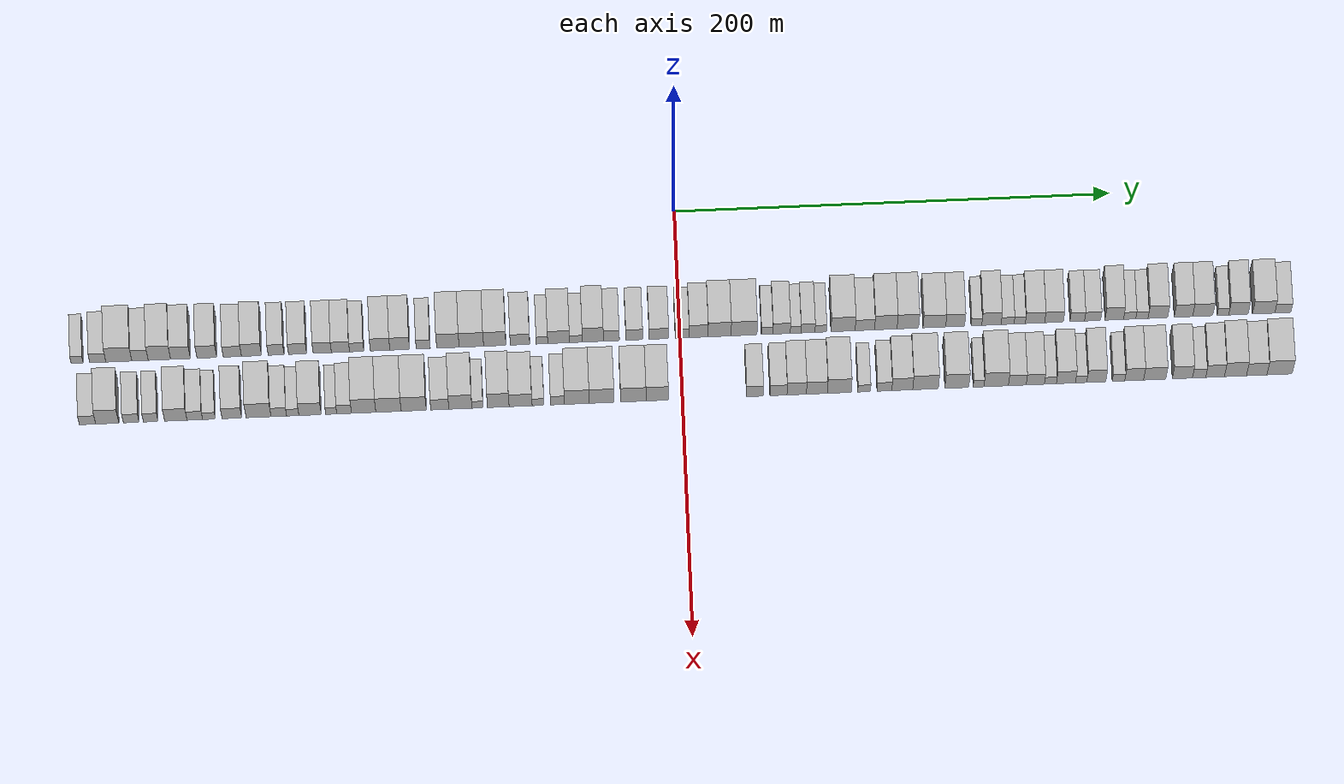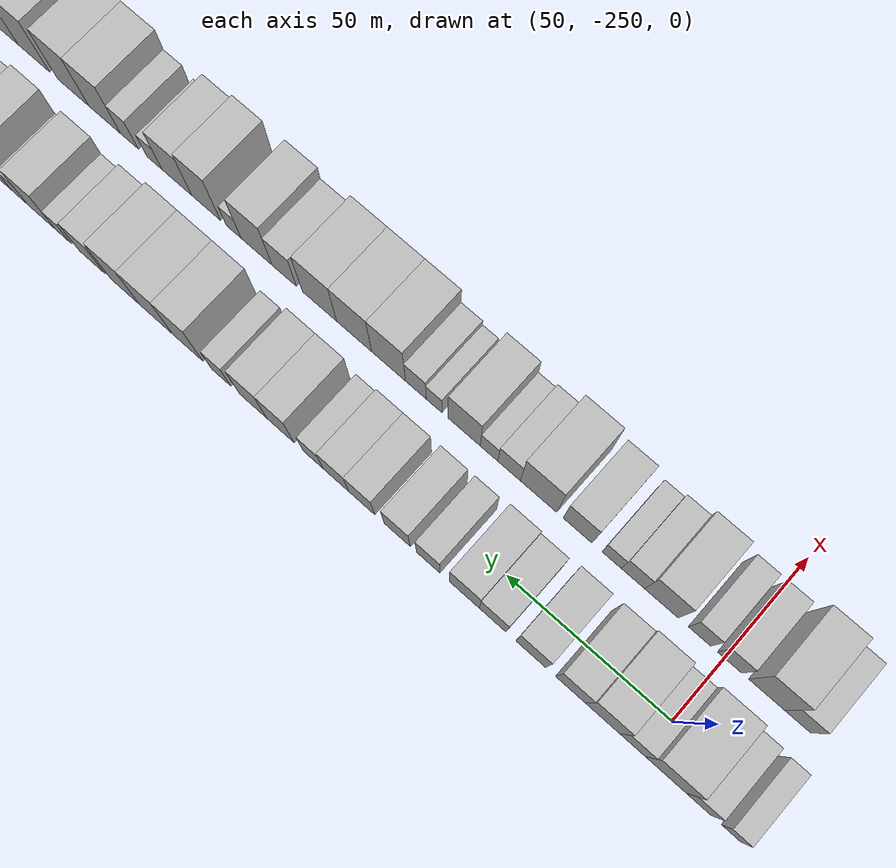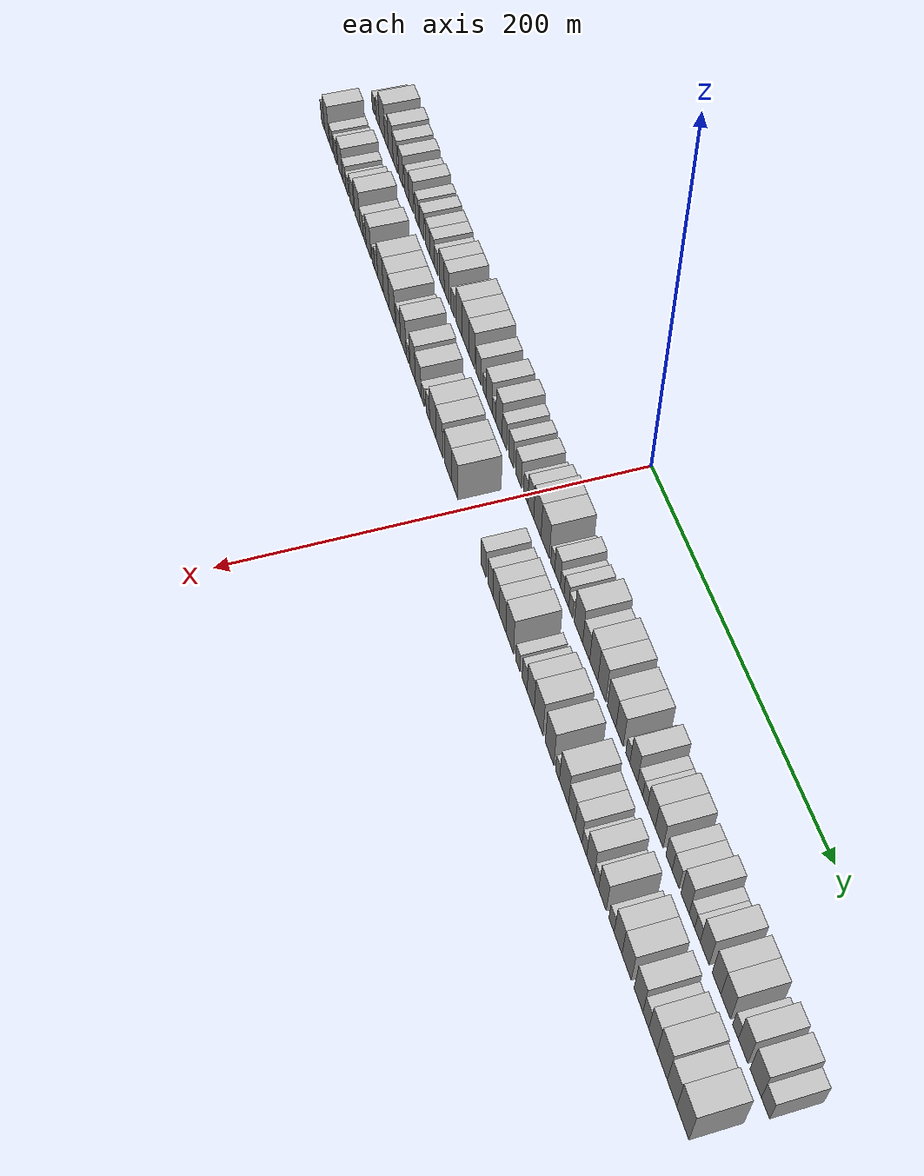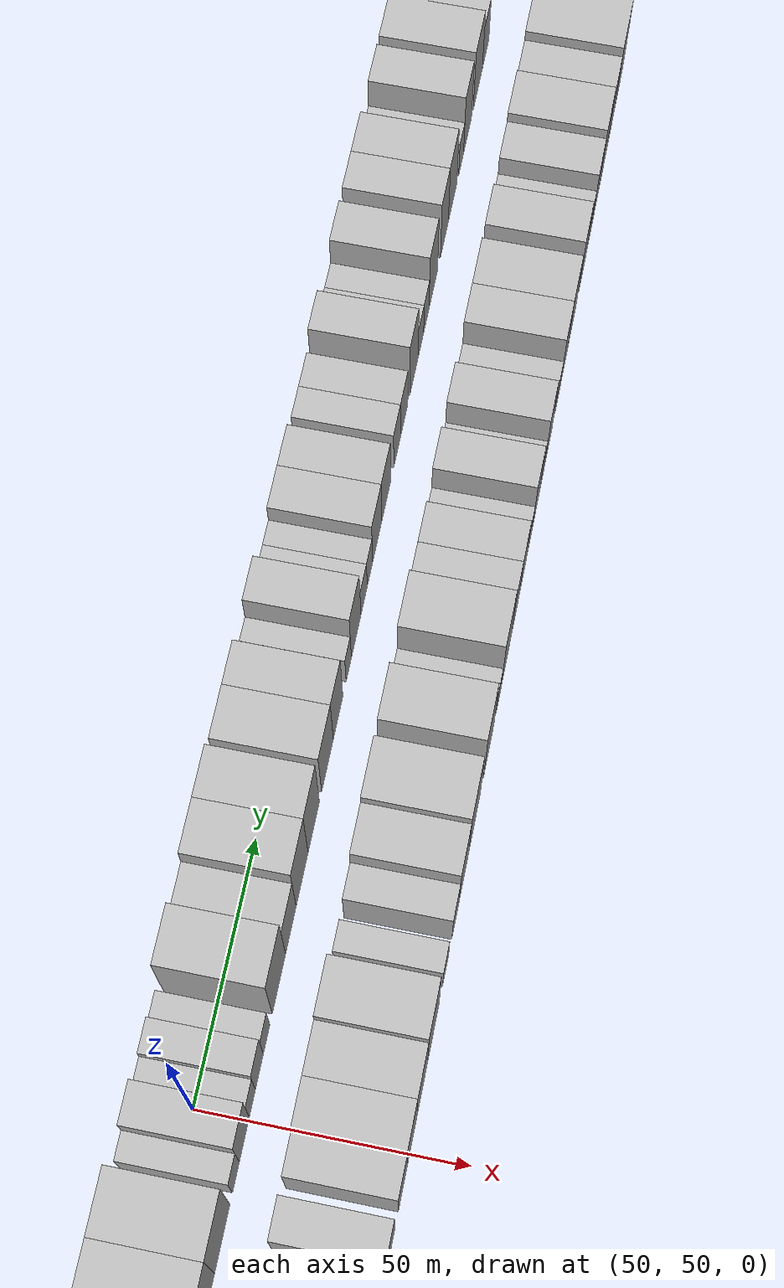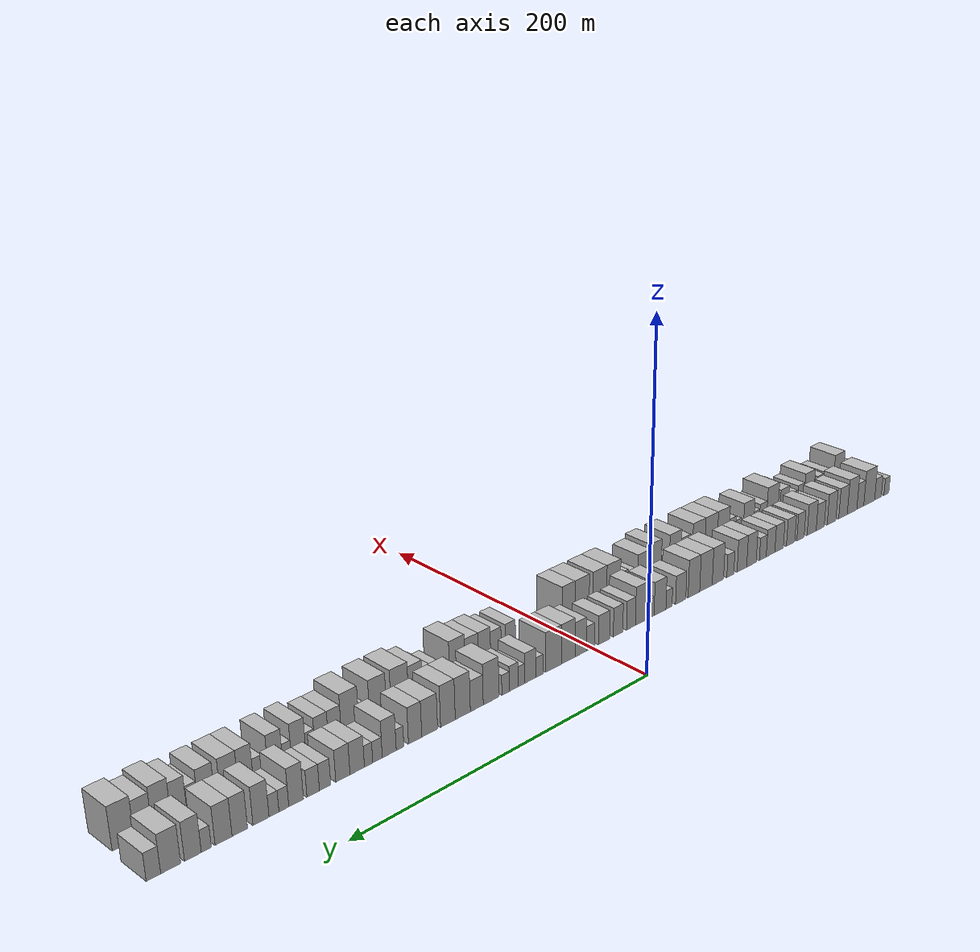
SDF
<sdf version="1.6">
 <world name="default">
  <scene>
   <sky><clouds><speed>12</speed></clouds></sky>
   <ambient>0.4 0.4 0.4 1</ambient>
   <background>0.7 0.7 0.7 1</background>
   <shadows>1</shadows>
  </scene>
  <gravity>0 0 -9.8066</gravity>
  <magnetic_field>6e-06 2.3e-05 -4.2e-05</magnetic_field>
  <physics default="0" name="default_physics" type="ode">
   <ode>
    <solver>
     <type>quick</type>
     <iters>10</iters>
     <sor>1.0</sor>
     <use_dynamic_moi_rescaling>0</use_dynamic_moi_rescaling>
    </solver>
    <constraints>
     <cfm>0</cfm>
     <erp>0.2</erp>
     <contact_max_correcting_vel>100</contact_max_correcting_vel>
     <contact_surface_layer>0.001</contact_surface_layer>
    </constraints>
   </ode>
   <max_step_size>0.004</max_step_size>
   <real_time_factor>1</real_time_factor>
   <real_time_update_rate>250</real_time_update_rate>
  </physics>
  <light name="sun" type="directional">
   <pose>0 0 10 0 0 0</pose>
   <diffuse>0.8 0.8 0.8 1</diffuse>
   <specular>0.2 0.2 0.2 1</specular>
   <attenuation>
    <range>1000</range>
    <constant>0.9</constant>
    <linear>0.01</linear>
    <quadratic>0.001</quadratic>
   </attenuation>
   <direction>-0.5 0.1 -0.9</direction>
  </light>
  <model name="building_1">
   <static>1</static>
   <pose>50.0000 -275.2284 0 0.000000 0.000000 0.000000</pose>
   <link name="link">
    <pose>0 0 6.00 0 0 0</pose>
    <collision name="collision"><geometry><box><size>20.0000 5.5433 12.0000</size></box></geometry></collision>
    <visual name="visual">
     <cast_shadows>0</cast_shadows>
     <geometry><box><size>20.0000 5.5433 12.0000</size></box></geometry>
     <material>
      <script>
       <uri>model://HANNAS_wall/materials/scripts</uri>
       <uri>model://HANNAS_wall/materials/textures</uri>
       <name>vrc/HANNAS_wall</name>
      </script>
     </material>
    </visual>
   </link>
  </model>
  <model name="building_2">
   <static>1</static>
   <pose>50.0000 -265.7888 0 0.000000 0.000000 0.000000</pose>
   <link name="link">
    <pose>0 0 7.50 0 0 0</pose>
    <collision name="collision"><geometry><box><size>20.0000 7.3357 15.0000</size></box></geometry></collision>
    <visual name="visual">
     <cast_shadows>0</cast_shadows>
     <geometry><box><size>20.0000 7.3357 15.0000</size></box></geometry>
     <material>
      <script>
       <uri>model://HANNAS_wall/materials/scripts</uri>
       <uri>model://HANNAS_wall/materials/textures</uri>
       <name>vrc/HANNAS_wall</name>
      </script>
     </material>
    </visual>
   </link>
  </model>
  <model name="building_3">
   <static>1</static>
   <pose>50.0000 -256.1935 0 0.000000 0.000000 0.000000</pose>
   <link name="link">
    <pose>0 0 12.00 0 0 0</pose>
    <collision name="collision"><geometry><box><size>20.0000 11.8549 24.0000</size></box></geometry></collision>
    <visual name="visual">
     <cast_shadows>0</cast_shadows>
     <geometry><box><size>20.0000 11.8549 24.0000</size></box></geometry>
     <material>
      <script>
       <uri>model://HANNAS_wall/materials/scripts</uri>
       <uri>model://HANNAS_wall/materials/textures</uri>
       <name>vrc/HANNAS_wall</name>
      </script>
     </material>
    </visual>
   </link>
  </model>
  <model name="building_4">
   <static>1</static>
   <pose>50.0000 -246.5376 0 0.000000 0.000000 0.000000</pose>
   <link name="link">
    <pose>0 0 9.00 0 0 0</pose>
    <collision name="collision"><geometry><box><size>20.0000 7.4569 18.0000</size></box></geometry></collision>
    <visual name="visual">
     <cast_shadows>0</cast_shadows>
     <geometry><box><size>20.0000 7.4569 18.0000</size></box></geometry>
     <material>
      <script>
       <uri>model://HANNAS_wall/materials/scripts</uri>
       <uri>model://HANNAS_wall/materials/textures</uri>
       <name>vrc/HANNAS_wall</name>
      </script>
     </material>
    </visual>
   </link>
  </model>
  <model name="building_5">
   <static>1</static>
   <pose>50.0000 -237.7016 0 0.000000 0.000000 0.000000</pose>
   <link name="link">
    <pose>0 0 12.00 0 0 0</pose>
    <collision name="collision"><geometry><box><size>20.0000 10.2150 24.0000</size></box></geometry></collision>
    <visual name="visual">
     <cast_shadows>0</cast_shadows>
     <geometry><box><size>20.0000 10.2150 24.0000</size></box></geometry>
     <material>
      <script>
       <uri>model://HANNAS_wall/materials/scripts</uri>
       <uri>model://HANNAS_wall/materials/textures</uri>
       <name>vrc/HANNAS_wall</name>
      </script>
     </material>
    </visual>
   </link>
  </model>
  <model name="building_6">
   <static>1</static>
   <pose>50.0000 -228.0764 0 0.000000 0.000000 0.000000</pose>
   <link name="link">
    <pose>0 0 10.50 0 0 0</pose>
    <collision name="collision"><geometry><box><size>20.0000 9.0354 21.0000</size></box></geometry></collision>
    <visual name="visual">
     <cast_shadows>0</cast_shadows>
     <geometry><box><size>20.0000 9.0354 21.0000</size></box></geometry>
     <material>
      <script>
       <uri>model://HANNAS_wall/materials/scripts</uri>
       <uri>model://HANNAS_wall/materials/textures</uri>
       <name>vrc/HANNAS_wall</name>
      </script>
     </material>
    </visual>
   </link>
  </model>
  <model name="building_7">
   <static>1</static>
   <pose>50.0000 -216.0344 0 0.000000 0.000000 0.000000</pose>
   <link name="link">
    <pose>0 0 10.50 0 0 0</pose>
    <collision name="collision"><geometry><box><size>20.0000 9.0486 21.0000</size></box></geometry></collision>
    <visual name="visual">
     <cast_shadows>0</cast_shadows>
     <geometry><box><size>20.0000 9.0486 21.0000</size></box></geometry>
     <material>
      <script>
       <uri>model://HANNAS_wall/materials/scripts</uri>
       <uri>model://HANNAS_wall/materials/textures</uri>
       <name>vrc/HANNAS_wall</name>
      </script>
     </material>
    </visual>
   </link>
  </model>
  <model name="building_8">
   <static>1</static>
   <pose>50.0000 -204.3660 0 0.000000 0.000000 0.000000</pose>
   <link name="link">
    <pose>0 0 9.00 0 0 0</pose>
    <collision name="collision"><geometry><box><size>20.0000 8.2883 18.0000</size></box></geometry></collision>
    <visual name="visual">
     <cast_shadows>0</cast_shadows>
     <geometry><box><size>20.0000 8.2883 18.0000</size></box></geometry>
     <material>
      <script>
       <uri>model://HANNAS_wall/materials/scripts</uri>
       <uri>model://HANNAS_wall/materials/textures</uri>
       <name>vrc/HANNAS_wall</name>
      </script>
     </material>
    </visual>
   </link>
  </model>
  <model name="building_9">
   <static>1</static>
   <pose>50.0000 -195.6271 0 0.000000 0.000000 0.000000</pose>
   <link name="link">
    <pose>0 0 10.50 0 0 0</pose>
    <collision name="collision"><geometry><box><size>20.0000 9.1893 21.0000</size></box></geometry></collision>
    <visual name="visual">
     <cast_shadows>0</cast_shadows>
     <geometry><box><size>20.0000 9.1893 21.0000</size></box></geometry>
     <material>
      <script>
       <uri>model://HANNAS_wall/materials/scripts</uri>
       <uri>model://HANNAS_wall/materials/textures</uri>
       <name>vrc/HANNAS_wall</name>
      </script>
     </material>
    </visual>
   </link>
  </model>
  <model name="building_10">
   <static>1</static>
   <pose>50.0000 -184.3791 0 0.000000 0.000000 0.000000</pose>
   <link name="link">
    <pose>0 0 9.00 0 0 0</pose>
    <collision name="collision"><geometry><box><size>20.0000 7.3068 18.0000</size></box></geometry></collision>
    <visual name="visual">
     <cast_shadows>0</cast_shadows>
     <geometry><box><size>20.0000 7.3068 18.0000</size></box></geometry>
     <material>
      <script>
       <uri>model://HANNAS_wall/materials/scripts</uri>
       <uri>model://HANNAS_wall/materials/textures</uri>
       <name>vrc/HANNAS_wall</name>
      </script>
     </material>
    </visual>
   </link>
  </model>
  <model name="building_11">
   <static>1</static>
   <pose>50.0000 -174.5817 0 0.000000 0.000000 0.000000</pose>
   <link name="link">
    <pose>0 0 9.00 0 0 0</pose>
    <collision name="collision"><geometry><box><size>20.0000 8.2879 18.0000</size></box></geometry></collision>
    <visual name="visual">
     <cast_shadows>0</cast_shadows>
     <geometry><box><size>20.0000 8.2879 18.0000</size></box></geometry>
     <material>
      <script>
       <uri>model://HANNAS_wall/materials/scripts</uri>
       <uri>model://HANNAS_wall/materials/textures</uri>
       <name>vrc/HANNAS_wall</name>
      </script>
     </material>
    </visual>
   </link>
  </model>
  <model name="building_12">
   <static>1</static>
   <pose>50.0000 -163.2917 0 0.000000 0.000000 0.000000</pose>
   <link name="link">
    <pose>0 0 9.00 0 0 0</pose>
    <collision name="collision"><geometry><box><size>20.0000 8.2921 18.0000</size></box></geometry></collision>
    <visual name="visual">
     <cast_shadows>0</cast_shadows>
     <geometry><box><size>20.0000 8.2921 18.0000</size></box></geometry>
     <material>
      <script>
       <uri>model://HANNAS_wall/materials/scripts</uri>
       <uri>model://HANNAS_wall/materials/textures</uri>
       <name>vrc/HANNAS_wall</name>
      </script>
     </material>
    </visual>
   </link>
  </model>
  <model name="building_13">
   <static>1</static>
   <pose>50.0000 -154.9882 0 0.000000 0.000000 0.000000</pose>
   <link name="link">
    <pose>0 0 9.00 0 0 0</pose>
    <collision name="collision"><geometry><box><size>20.0000 8.3149 18.0000</size></box></geometry></collision>
    <visual name="visual">
     <cast_shadows>0</cast_shadows>
     <geometry><box><size>20.0000 8.3149 18.0000</size></box></geometry>
     <material>
      <script>
       <uri>model://HANNAS_wall/materials/scripts</uri>
       <uri>model://HANNAS_wall/materials/textures</uri>
       <name>vrc/HANNAS_wall</name>
      </script>
     </material>
    </visual>
   </link>
  </model>
  <model name="building_14">
   <static>1</static>
   <pose>50.0000 -147.5712 0 0.000000 0.000000 0.000000</pose>
   <link name="link">
    <pose>0 0 7.50 0 0 0</pose>
    <collision name="collision"><geometry><box><size>20.0000 6.5192 15.0000</size></box></geometry></collision>
    <visual name="visual">
     <cast_shadows>0</cast_shadows>
     <geometry><box><size>20.0000 6.5192 15.0000</size></box></geometry>
     <material>
      <script>
       <uri>model://HANNAS_wall/materials/scripts</uri>
       <uri>model://HANNAS_wall/materials/textures</uri>
       <name>vrc/HANNAS_wall</name>
      </script>
     </material>
    </visual>
   </link>
  </model>
  <model name="building_15">
   <static>1</static>
   <pose>50.0000 -136.8504 0 0.000000 0.000000 0.000000</pose>
   <link name="link">
    <pose>0 0 10.50 0 0 0</pose>
    <collision name="collision"><geometry><box><size>20.0000 8.9223 21.0000</size></box></geometry></collision>
    <visual name="visual">
     <cast_shadows>0</cast_shadows>
     <geometry><box><size>20.0000 8.9223 21.0000</size></box></geometry>
     <material>
      <script>
       <uri>model://HANNAS_wall/materials/scripts</uri>
       <uri>model://HANNAS_wall/materials/textures</uri>
       <name>vrc/HANNAS_wall</name>
      </script>
     </material>
    </visual>
   </link>
  </model>
  <model name="building_16">
   <static>1</static>
   <pose>50.0000 -127.8862 0 0.000000 0.000000 0.000000</pose>
   <link name="link">
    <pose>0 0 10.50 0 0 0</pose>
    <collision name="collision"><geometry><box><size>20.0000 9.0061 21.0000</size></box></geometry></collision>
    <visual name="visual">
     <cast_shadows>0</cast_shadows>
     <geometry><box><size>20.0000 9.0061 21.0000</size></box></geometry>
     <material>
      <script>
       <uri>model://HANNAS_wall/materials/scripts</uri>
       <uri>model://HANNAS_wall/materials/textures</uri>
       <name>vrc/HANNAS_wall</name>
      </script>
     </material>
    </visual>
   </link>
  </model>
  <model name="building_17">
   <static>1</static>
   <pose>50.0000 -117.1879 0 0.000000 0.000000 0.000000</pose>
   <link name="link">
    <pose>0 0 7.50 0 0 0</pose>
    <collision name="collision"><geometry><box><size>20.0000 6.3906 15.0000</size></box></geometry></collision>
    <visual name="visual">
     <cast_shadows>0</cast_shadows>
     <geometry><box><size>20.0000 6.3906 15.0000</size></box></geometry>
     <material>
      <script>
       <uri>model://HANNAS_wall/materials/scripts</uri>
       <uri>model://HANNAS_wall/materials/textures</uri>
       <name>vrc/HANNAS_wall</name>
      </script>
     </material>
    </visual>
   </link>
  </model>
  <model name="building_18">
   <static>1</static>
   <pose>50.0000 -105.8745 0 0.000000 0.000000 0.000000</pose>
   <link name="link">
    <pose>0 0 12.00 0 0 0</pose>
    <collision name="collision"><geometry><box><size>20.0000 10.2362 24.0000</size></box></geometry></collision>
    <visual name="visual">
     <cast_shadows>0</cast_shadows>
     <geometry><box><size>20.0000 10.2362 24.0000</size></box></geometry>
     <material>
      <script>
       <uri>model://HANNAS_wall/materials/scripts</uri>
       <uri>model://HANNAS_wall/materials/textures</uri>
       <name>vrc/HANNAS_wall</name>
      </script>
     </material>
    </visual>
   </link>
  </model>
  <model name="building_19">
   <static>1</static>
   <pose>50.0000 -95.1828 0 0.000000 0.000000 0.000000</pose>
   <link name="link">
    <pose>0 0 12.00 0 0 0</pose>
    <collision name="collision"><geometry><box><size>20.0000 11.1471 24.0000</size></box></geometry></collision>
    <visual name="visual">
     <cast_shadows>0</cast_shadows>
     <geometry><box><size>20.0000 11.1471 24.0000</size></box></geometry>
     <material>
      <script>
       <uri>model://HANNAS_wall/materials/scripts</uri>
       <uri>model://HANNAS_wall/materials/textures</uri>
       <name>vrc/HANNAS_wall</name>
      </script>
     </material>
    </visual>
   </link>
  </model>
  <model name="building_20">
   <static>1</static>
   <pose>50.0000 -84.5005 0 0.000000 0.000000 0.000000</pose>
   <link name="link">
    <pose>0 0 12.00 0 0 0</pose>
    <collision name="collision"><geometry><box><size>20.0000 10.2175 24.0000</size></box></geometry></collision>
    <visual name="visual">
     <cast_shadows>0</cast_shadows>
     <geometry><box><size>20.0000 10.2175 24.0000</size></box></geometry>
     <material>
      <script>
       <uri>model://HANNAS_wall/materials/scripts</uri>
       <uri>model://HANNAS_wall/materials/textures</uri>
       <name>vrc/HANNAS_wall</name>
      </script>
     </material>
    </visual>
   </link>
  </model>
  <model name="building_21">
   <static>1</static>
   <pose>50.0000 -72.9549 0 0.000000 0.000000 0.000000</pose>
   <link name="link">
    <pose>0 0 9.00 0 0 0</pose>
    <collision name="collision"><geometry><box><size>20.0000 8.8736 18.0000</size></box></geometry></collision>
    <visual name="visual">
     <cast_shadows>0</cast_shadows>
     <geometry><box><size>20.0000 8.8736 18.0000</size></box></geometry>
     <material>
      <script>
       <uri>model://HANNAS_wall/materials/scripts</uri>
       <uri>model://HANNAS_wall/materials/textures</uri>
       <name>vrc/HANNAS_wall</name>
      </script>
     </material>
    </visual>
   </link>
  </model>
  <model name="building_22">
   <static>1</static>
   <pose>50.0000 -62.8980 0 0.000000 0.000000 0.000000</pose>
   <link name="link">
    <pose>0 0 6.00 0 0 0</pose>
    <collision name="collision"><geometry><box><size>20.0000 5.2403 12.0000</size></box></geometry></collision>
    <visual name="visual">
     <cast_shadows>0</cast_shadows>
     <geometry><box><size>20.0000 5.2403 12.0000</size></box></geometry>
     <material>
      <script>
       <uri>model://HANNAS_wall/materials/scripts</uri>
       <uri>model://HANNAS_wall/materials/textures</uri>
       <name>vrc/HANNAS_wall</name>
      </script>
     </material>
    </visual>
   </link>
  </model>
  <model name="building_23">
   <static>1</static>
   <pose>50.0000 -55.2958 0 0.000000 0.000000 0.000000</pose>
   <link name="link">
    <pose>0 0 10.50 0 0 0</pose>
    <collision name="collision"><geometry><box><size>20.0000 9.9641 21.0000</size></box></geometry></collision>
    <visual name="visual">
     <cast_shadows>0</cast_shadows>
     <geometry><box><size>20.0000 9.9641 21.0000</size></box></geometry>
     <material>
      <script>
       <uri>model://HANNAS_wall/materials/scripts</uri>
       <uri>model://HANNAS_wall/materials/textures</uri>
       <name>vrc/HANNAS_wall</name>
      </script>
     </material>
    </visual>
   </link>
  </model>
  <model name="building_24">
   <static>1</static>
   <pose>50.0000 -47.3811 0 0.000000 0.000000 0.000000</pose>
   <link name="link">
    <pose>0 0 6.00 0 0 0</pose>
    <collision name="collision"><geometry><box><size>20.0000 5.8652 12.0000</size></box></geometry></collision>
    <visual name="visual">
     <cast_shadows>0</cast_shadows>
     <geometry><box><size>20.0000 5.8652 12.0000</size></box></geometry>
     <material>
      <script>
       <uri>model://HANNAS_wall/materials/scripts</uri>
       <uri>model://HANNAS_wall/materials/textures</uri>
       <name>vrc/HANNAS_wall</name>
      </script>
     </material>
    </visual>
   </link>
  </model>
  <model name="building_25">
   <static>1</static>
   <pose>50.0000 -39.6424 0 0.000000 0.000000 0.000000</pose>
   <link name="link">
    <pose>0 0 12.00 0 0 0</pose>
    <collision name="collision"><geometry><box><size>20.0000 9.6122 24.0000</size></box></geometry></collision>
    <visual name="visual">
     <cast_shadows>0</cast_shadows>
     <geometry><box><size>20.0000 9.6122 24.0000</size></box></geometry>
     <material>
      <script>
       <uri>model://HANNAS_wall/materials/scripts</uri>
       <uri>model://HANNAS_wall/materials/textures</uri>
       <name>vrc/HANNAS_wall</name>
      </script>
     </material>
    </visual>
   </link>
  </model>
  <model name="building_26">
   <static>1</static>
   <pose>50.0000 -31.1935 0 0.000000 0.000000 0.000000</pose>
   <link name="link">
    <pose>0 0 9.00 0 0 0</pose>
    <collision name="collision"><geometry><box><size>20.0000 7.2858 18.0000</size></box></geometry></collision>
    <visual name="visual">
     <cast_shadows>0</cast_shadows>
     <geometry><box><size>20.0000 7.2858 18.0000</size></box></geometry>
     <material>
      <script>
       <uri>model://HANNAS_wall/materials/scripts</uri>
       <uri>model://HANNAS_wall/materials/textures</uri>
       <name>vrc/HANNAS_wall</name>
      </script>
     </material>
    </visual>
   </link>
  </model>
  <model name="building_27">
   <static>1</static>
   <pose>50.0000 -20.7220 0 0.000000 0.000000 0.000000</pose>
   <link name="link">
    <pose>0 0 9.00 0 0 0</pose>
    <collision name="collision"><geometry><box><size>20.0000 7.6572 18.0000</size></box></geometry></collision>
    <visual name="visual">
     <cast_shadows>0</cast_shadows>
     <geometry><box><size>20.0000 7.6572 18.0000</size></box></geometry>
     <material>
      <script>
       <uri>model://HANNAS_wall/materials/scripts</uri>
       <uri>model://HANNAS_wall/materials/textures</uri>
       <name>vrc/HANNAS_wall</name>
      </script>
     </material>
    </visual>
   </link>
  </model>
  <model name="building_28">
   <static>1</static>
   <pose>50.0000 -9.4502 0 0.000000 0.000000 0.000000</pose>
   <link name="link">
    <pose>0 0 9.00 0 0 0</pose>
    <collision name="collision"><geometry><box><size>20.0000 8.8863 18.0000</size></box></geometry></collision>
    <visual name="visual">
     <cast_shadows>0</cast_shadows>
     <geometry><box><size>20.0000 8.8863 18.0000</size></box></geometry>
     <material>
      <script>
       <uri>model://HANNAS_wall/materials/scripts</uri>
       <uri>model://HANNAS_wall/materials/textures</uri>
       <name>vrc/HANNAS_wall</name>
      </script>
     </material>
    </visual>
   </link>
  </model>
  <model name="building_29">
   <static>1</static>
   <pose>50.0000 1.1949 0 0.000000 0.000000 0.000000</pose>
   <link name="link">
    <pose>0 0 7.50 0 0 0</pose>
    <collision name="collision"><geometry><box><size>20.0000 6.4039 15.0000</size></box></geometry></collision>
    <visual name="visual">
     <cast_shadows>0</cast_shadows>
     <geometry><box><size>20.0000 6.4039 15.0000</size></box></geometry>
     <material>
      <script>
       <uri>model://HANNAS_wall/materials/scripts</uri>
       <uri>model://HANNAS_wall/materials/textures</uri>
       <name>vrc/HANNAS_wall</name>
      </script>
     </material>
    </visual>
   </link>
  </model>
  <model name="building_30">
   <static>1</static>
   <pose>50.0000 8.7194 0 0.000000 0.000000 0.000000</pose>
   <link name="link">
    <pose>0 0 10.50 0 0 0</pose>
    <collision name="collision"><geometry><box><size>20.0000 8.6451 21.0000</size></box></geometry></collision>
    <visual name="visual">
     <cast_shadows>0</cast_shadows>
     <geometry><box><size>20.0000 8.6451 21.0000</size></box></geometry>
     <material>
      <script>
       <uri>model://HANNAS_wall/materials/scripts</uri>
       <uri>model://HANNAS_wall/materials/textures</uri>
       <name>vrc/HANNAS_wall</name>
      </script>
     </material>
    </visual>
   </link>
  </model>
  <model name="building_31">
   <static>1</static>
   <pose>50.0000 18.3045 0 0.000000 0.000000 0.000000</pose>
   <link name="link">
    <pose>0 0 12.00 0 0 0</pose>
    <collision name="collision"><geometry><box><size>20.0000 10.5250 24.0000</size></box></geometry></collision>
    <visual name="visual">
     <cast_shadows>0</cast_shadows>
     <geometry><box><size>20.0000 10.5250 24.0000</size></box></geometry>
     <material>
      <script>
       <uri>model://HANNAS_wall/materials/scripts</uri>
       <uri>model://HANNAS_wall/materials/textures</uri>
       <name>vrc/HANNAS_wall</name>
      </script>
     </material>
    </visual>
   </link>
  </model>
  <model name="building_32">
   <static>1</static>
   <pose>50.0000 29.4682 0 0.000000 0.000000 0.000000</pose>
   <link name="link">
    <pose>0 0 12.00 0 0 0</pose>
    <collision name="collision"><geometry><box><size>20.0000 11.8026 24.0000</size></box></geometry></collision>
    <visual name="visual">
     <cast_shadows>0</cast_shadows>
     <geometry><box><size>20.0000 11.8026 24.0000</size></box></geometry>
     <material>
      <script>
       <uri>model://HANNAS_wall/materials/scripts</uri>
       <uri>model://HANNAS_wall/materials/textures</uri>
       <name>vrc/HANNAS_wall</name>
      </script>
     </material>
    </visual>
   </link>
  </model>
  <model name="building_33">
   <static>1</static>
   <pose>50.0000 40.0269 0 0.000000 0.000000 0.000000</pose>
   <link name="link">
    <pose>0 0 6.00 0 0 0</pose>
    <collision name="collision"><geometry><box><size>20.0000 5.3147 12.0000</size></box></geometry></collision>
    <visual name="visual">
     <cast_shadows>0</cast_shadows>
     <geometry><box><size>20.0000 5.3147 12.0000</size></box></geometry>
     <material>
      <script>
       <uri>model://HANNAS_wall/materials/scripts</uri>
       <uri>model://HANNAS_wall/materials/textures</uri>
       <name>vrc/HANNAS_wall</name>
      </script>
     </material>
    </visual>
   </link>
  </model>
  <model name="building_34">
   <static>1</static>
   <pose>50.0000 46.6303 0 0.000000 0.000000 0.000000</pose>
   <link name="link">
    <pose>0 0 9.00 0 0 0</pose>
    <collision name="collision"><geometry><box><size>20.0000 7.8922 18.0000</size></box></geometry></collision>
    <visual name="visual">
     <cast_shadows>0</cast_shadows>
     <geometry><box><size>20.0000 7.8922 18.0000</size></box></geometry>
     <material>
      <script>
       <uri>model://HANNAS_wall/materials/scripts</uri>
       <uri>model://HANNAS_wall/materials/textures</uri>
       <name>vrc/HANNAS_wall</name>
      </script>
     </material>
    </visual>
   </link>
  </model>
  <model name="building_35">
   <static>1</static>
   <pose>50.0000 53.0246 0 0.000000 0.000000 0.000000</pose>
   <link name="link">
    <pose>0 0 6.00 0 0 0</pose>
    <collision name="collision"><geometry><box><size>20.0000 4.8964 12.0000</size></box></geometry></collision>
    <visual name="visual">
     <cast_shadows>0</cast_shadows>
     <geometry><box><size>20.0000 4.8964 12.0000</size></box></geometry>
     <material>
      <script>
       <uri>model://HANNAS_wall/materials/scripts</uri>
       <uri>model://HANNAS_wall/materials/textures</uri>
       <name>vrc/HANNAS_wall</name>
      </script>
     </material>
    </visual>
   </link>
  </model>
  <model name="building_36">
   <static>1</static>
   <pose>50.0000 58.6801 0 0.000000 0.000000 0.000000</pose>
   <link name="link">
    <pose>0 0 7.50 0 0 0</pose>
    <collision name="collision"><geometry><box><size>20.0000 6.4146 15.0000</size></box></geometry></collision>
    <visual name="visual">
     <cast_shadows>0</cast_shadows>
     <geometry><box><size>20.0000 6.4146 15.0000</size></box></geometry>
     <material>
      <script>
       <uri>model://HANNAS_wall/materials/scripts</uri>
       <uri>model://HANNAS_wall/materials/textures</uri>
       <name>vrc/HANNAS_wall</name>
      </script>
     </material>
    </visual>
   </link>
  </model>
  <model name="building_37">
   <static>1</static>
   <pose>50.0000 64.5308 0 0.000000 0.000000 0.000000</pose>
   <link name="link">
    <pose>0 0 6.00 0 0 0</pose>
    <collision name="collision"><geometry><box><size>20.0000 5.2868 12.0000</size></box></geometry></collision>
    <visual name="visual">
     <cast_shadows>0</cast_shadows>
     <geometry><box><size>20.0000 5.2868 12.0000</size></box></geometry>
     <material>
      <script>
       <uri>model://HANNAS_wall/materials/scripts</uri>
       <uri>model://HANNAS_wall/materials/textures</uri>
       <name>vrc/HANNAS_wall</name>
      </script>
     </material>
    </visual>
   </link>
  </model>
  <model name="building_38">
   <static>1</static>
   <pose>50.0000 74.7071 0 0.000000 0.000000 0.000000</pose>
   <link name="link">
    <pose>0 0 12.00 0 0 0</pose>
    <collision name="collision"><geometry><box><size>20.0000 11.0657 24.0000</size></box></geometry></collision>
    <visual name="visual">
     <cast_shadows>0</cast_shadows>
     <geometry><box><size>20.0000 11.0657 24.0000</size></box></geometry>
     <material>
      <script>
       <uri>model://HANNAS_wall/materials/scripts</uri>
       <uri>model://HANNAS_wall/materials/textures</uri>
       <name>vrc/HANNAS_wall</name>
      </script>
     </material>
    </visual>
   </link>
  </model>
  <model name="building_39">
   <static>1</static>
   <pose>50.0000 84.6900 0 0.000000 0.000000 0.000000</pose>
   <link name="link">
    <pose>0 0 9.00 0 0 0</pose>
    <collision name="collision"><geometry><box><size>20.0000 8.9002 18.0000</size></box></geometry></collision>
    <visual name="visual">
     <cast_shadows>0</cast_shadows>
     <geometry><box><size>20.0000 8.9002 18.0000</size></box></geometry>
     <material>
      <script>
       <uri>model://HANNAS_wall/materials/scripts</uri>
       <uri>model://HANNAS_wall/materials/textures</uri>
       <name>vrc/HANNAS_wall</name>
      </script>
     </material>
    </visual>
   </link>
  </model>
  <model name="building_40">
   <static>1</static>
   <pose>50.0000 94.2811 0 0.000000 0.000000 0.000000</pose>
   <link name="link">
    <pose>0 0 12.00 0 0 0</pose>
    <collision name="collision"><geometry><box><size>20.0000 10.2821 24.0000</size></box></geometry></collision>
    <visual name="visual">
     <cast_shadows>0</cast_shadows>
     <geometry><box><size>20.0000 10.2821 24.0000</size></box></geometry>
     <material>
      <script>
       <uri>model://HANNAS_wall/materials/scripts</uri>
       <uri>model://HANNAS_wall/materials/textures</uri>
       <name>vrc/HANNAS_wall</name>
      </script>
     </material>
    </visual>
   </link>
  </model>
  <model name="building_41">
   <static>1</static>
   <pose>50.0000 104.3454 0 0.000000 0.000000 0.000000</pose>
   <link name="link">
    <pose>0 0 12.00 0 0 0</pose>
    <collision name="collision"><geometry><box><size>20.0000 9.8465 24.0000</size></box></geometry></collision>
    <visual name="visual">
     <cast_shadows>0</cast_shadows>
     <geometry><box><size>20.0000 9.8465 24.0000</size></box></geometry>
     <material>
      <script>
       <uri>model://HANNAS_wall/materials/scripts</uri>
       <uri>model://HANNAS_wall/materials/textures</uri>
       <name>vrc/HANNAS_wall</name>
      </script>
     </material>
    </visual>
   </link>
  </model>
  <model name="building_42">
   <static>1</static>
   <pose>50.0000 116.4671 0 0.000000 0.000000 0.000000</pose>
   <link name="link">
    <pose>0 0 10.50 0 0 0</pose>
    <collision name="collision"><geometry><box><size>20.0000 10.3969 21.0000</size></box></geometry></collision>
    <visual name="visual">
     <cast_shadows>0</cast_shadows>
     <geometry><box><size>20.0000 10.3969 21.0000</size></box></geometry>
     <material>
      <script>
       <uri>model://HANNAS_wall/materials/scripts</uri>
       <uri>model://HANNAS_wall/materials/textures</uri>
       <name>vrc/HANNAS_wall</name>
      </script>
     </material>
    </visual>
   </link>
  </model>
  <model name="building_43">
   <static>1</static>
   <pose>50.0000 125.9778 0 0.000000 0.000000 0.000000</pose>
   <link name="link">
    <pose>0 0 10.50 0 0 0</pose>
    <collision name="collision"><geometry><box><size>20.0000 8.6244 21.0000</size></box></geometry></collision>
    <visual name="visual">
     <cast_shadows>0</cast_shadows>
     <geometry><box><size>20.0000 8.6244 21.0000</size></box></geometry>
     <material>
      <script>
       <uri>model://HANNAS_wall/materials/scripts</uri>
       <uri>model://HANNAS_wall/materials/textures</uri>
       <name>vrc/HANNAS_wall</name>
      </script>
     </material>
    </visual>
   </link>
  </model>
  <model name="building_44">
   <static>1</static>
   <pose>50.0000 135.7127 0 0.000000 0.000000 0.000000</pose>
   <link name="link">
    <pose>0 0 6.00 0 0 0</pose>
    <collision name="collision"><geometry><box><size>20.0000 4.8454 12.0000</size></box></geometry></collision>
    <visual name="visual">
     <cast_shadows>0</cast_shadows>
     <geometry><box><size>20.0000 4.8454 12.0000</size></box></geometry>
     <material>
      <script>
       <uri>model://HANNAS_wall/materials/scripts</uri>
       <uri>model://HANNAS_wall/materials/textures</uri>
       <name>vrc/HANNAS_wall</name>
      </script>
     </material>
    </visual>
   </link>
  </model>
  <model name="building_45">
   <static>1</static>
   <pose>50.0000 142.5539 0 0.000000 0.000000 0.000000</pose>
   <link name="link">
    <pose>0 0 10.50 0 0 0</pose>
    <collision name="collision"><geometry><box><size>20.0000 8.8371 21.0000</size></box></geometry></collision>
    <visual name="visual">
     <cast_shadows>0</cast_shadows>
     <geometry><box><size>20.0000 8.8371 21.0000</size></box></geometry>
     <material>
      <script>
       <uri>model://HANNAS_wall/materials/scripts</uri>
       <uri>model://HANNAS_wall/materials/textures</uri>
       <name>vrc/HANNAS_wall</name>
      </script>
     </material>
    </visual>
   </link>
  </model>
  <model name="building_46">
   <static>1</static>
   <pose>50.0000 149.9584 0 0.000000 0.000000 0.000000</pose>
   <link name="link">
    <pose>0 0 6.00 0 0 0</pose>
    <collision name="collision"><geometry><box><size>20.0000 5.9719 12.0000</size></box></geometry></collision>
    <visual name="visual">
     <cast_shadows>0</cast_shadows>
     <geometry><box><size>20.0000 5.9719 12.0000</size></box></geometry>
     <material>
      <script>
       <uri>model://HANNAS_wall/materials/scripts</uri>
       <uri>model://HANNAS_wall/materials/textures</uri>
       <name>vrc/HANNAS_wall</name>
      </script>
     </material>
    </visual>
   </link>
  </model>
  <model name="building_47">
   <static>1</static>
   <pose>50.0000 155.5113 0 0.000000 0.000000 0.000000</pose>
   <link name="link">
    <pose>0 0 6.00 0 0 0</pose>
    <collision name="collision"><geometry><box><size>20.0000 5.1338 12.0000</size></box></geometry></collision>
    <visual name="visual">
     <cast_shadows>0</cast_shadows>
     <geometry><box><size>20.0000 5.1338 12.0000</size></box></geometry>
     <material>
      <script>
       <uri>model://HANNAS_wall/materials/scripts</uri>
       <uri>model://HANNAS_wall/materials/textures</uri>
       <name>vrc/HANNAS_wall</name>
      </script>
     </material>
    </visual>
   </link>
  </model>
  <model name="building_48">
   <static>1</static>
   <pose>50.0000 162.5035 0 0.000000 0.000000 0.000000</pose>
   <link name="link">
    <pose>0 0 9.00 0 0 0</pose>
    <collision name="collision"><geometry><box><size>20.0000 8.8507 18.0000</size></box></geometry></collision>
    <visual name="visual">
     <cast_shadows>0</cast_shadows>
     <geometry><box><size>20.0000 8.8507 18.0000</size></box></geometry>
     <material>
      <script>
       <uri>model://HANNAS_wall/materials/scripts</uri>
       <uri>model://HANNAS_wall/materials/textures</uri>
       <name>vrc/HANNAS_wall</name>
      </script>
     </material>
    </visual>
   </link>
  </model>
  <model name="building_49">
   <static>1</static>
   <pose>50.0000 171.2219 0 0.000000 0.000000 0.000000</pose>
   <link name="link">
    <pose>0 0 9.00 0 0 0</pose>
    <collision name="collision"><geometry><box><size>20.0000 8.5860 18.0000</size></box></geometry></collision>
    <visual name="visual">
     <cast_shadows>0</cast_shadows>
     <geometry><box><size>20.0000 8.5860 18.0000</size></box></geometry>
     <material>
      <script>
       <uri>model://HANNAS_wall/materials/scripts</uri>
       <uri>model://HANNAS_wall/materials/textures</uri>
       <name>vrc/HANNAS_wall</name>
      </script>
     </material>
    </visual>
   </link>
  </model>
  <model name="building_50">
   <static>1</static>
   <pose>50.0000 181.8632 0 0.000000 0.000000 0.000000</pose>
   <link name="link">
    <pose>0 0 7.50 0 0 0</pose>
    <collision name="collision"><geometry><box><size>20.0000 6.6967 15.0000</size></box></geometry></collision>
    <visual name="visual">
     <cast_shadows>0</cast_shadows>
     <geometry><box><size>20.0000 6.6967 15.0000</size></box></geometry>
     <material>
      <script>
       <uri>model://HANNAS_wall/materials/scripts</uri>
       <uri>model://HANNAS_wall/materials/textures</uri>
       <name>vrc/HANNAS_wall</name>
      </script>
     </material>
    </visual>
   </link>
  </model>
  <model name="building_51">
   <static>1</static>
   <pose>50.0000 188.8856 0 0.000000 0.000000 0.000000</pose>
   <link name="link">
    <pose>0 0 7.50 0 0 0</pose>
    <collision name="collision"><geometry><box><size>20.0000 7.3482 15.0000</size></box></geometry></collision>
    <visual name="visual">
     <cast_shadows>0</cast_shadows>
     <geometry><box><size>20.0000 7.3482 15.0000</size></box></geometry>
     <material>
      <script>
       <uri>model://HANNAS_wall/materials/scripts</uri>
       <uri>model://HANNAS_wall/materials/textures</uri>
       <name>vrc/HANNAS_wall</name>
      </script>
     </material>
    </visual>
   </link>
  </model>
  <model name="building_52">
   <static>1</static>
   <pose>50.0000 198.8097 0 0.000000 0.000000 0.000000</pose>
   <link name="link">
    <pose>0 0 10.50 0 0 0</pose>
    <collision name="collision"><geometry><box><size>20.0000 8.5000 21.0000</size></box></geometry></collision>
    <visual name="visual">
     <cast_shadows>0</cast_shadows>
     <geometry><box><size>20.0000 8.5000 21.0000</size></box></geometry>
     <material>
      <script>
       <uri>model://HANNAS_wall/materials/scripts</uri>
       <uri>model://HANNAS_wall/materials/textures</uri>
       <name>vrc/HANNAS_wall</name>
      </script>
     </material>
    </visual>
   </link>
  </model>
  <model name="building_53">
   <static>1</static>
   <pose>50.0000 205.8723 0 0.000000 0.000000 0.000000</pose>
   <link name="link">
    <pose>0 0 6.00 0 0 0</pose>
    <collision name="collision"><geometry><box><size>20.0000 5.6251 12.0000</size></box></geometry></collision>
    <visual name="visual">
     <cast_shadows>0</cast_shadows>
     <geometry><box><size>20.0000 5.6251 12.0000</size></box></geometry>
     <material>
      <script>
       <uri>model://HANNAS_wall/materials/scripts</uri>
       <uri>model://HANNAS_wall/materials/textures</uri>
       <name>vrc/HANNAS_wall</name>
      </script>
     </material>
    </visual>
   </link>
  </model>
  <model name="building_54">
   <static>1</static>
   <pose>50.0000 211.4759 0 0.000000 0.000000 0.000000</pose>
   <link name="link">
    <pose>0 0 6.00 0 0 0</pose>
    <collision name="collision"><geometry><box><size>20.0000 5.5822 12.0000</size></box></geometry></collision>
    <visual name="visual">
     <cast_shadows>0</cast_shadows>
     <geometry><box><size>20.0000 5.5822 12.0000</size></box></geometry>
     <material>
      <script>
       <uri>model://HANNAS_wall/materials/scripts</uri>
       <uri>model://HANNAS_wall/materials/textures</uri>
       <name>vrc/HANNAS_wall</name>
      </script>
     </material>
    </visual>
   </link>
  </model>
  <model name="building_55">
   <static>1</static>
   <pose>50.0000 218.7514 0 0.000000 0.000000 0.000000</pose>
   <link name="link">
    <pose>0 0 10.50 0 0 0</pose>
    <collision name="collision"><geometry><box><size>20.0000 8.9689 21.0000</size></box></geometry></collision>
    <visual name="visual">
     <cast_shadows>0</cast_shadows>
     <geometry><box><size>20.0000 8.9689 21.0000</size></box></geometry>
     <material>
      <script>
       <uri>model://HANNAS_wall/materials/scripts</uri>
       <uri>model://HANNAS_wall/materials/textures</uri>
       <name>vrc/HANNAS_wall</name>
      </script>
     </material>
    </visual>
   </link>
  </model>
  <model name="building_56">
   <static>1</static>
   <pose>50.0000 230.4729 0 0.000000 0.000000 0.000000</pose>
   <link name="link">
    <pose>0 0 10.50 0 0 0</pose>
    <collision name="collision"><geometry><box><size>20.0000 8.4740 21.0000</size></box></geometry></collision>
    <visual name="visual">
     <cast_shadows>0</cast_shadows>
     <geometry><box><size>20.0000 8.4740 21.0000</size></box></geometry>
     <material>
      <script>
       <uri>model://HANNAS_wall/materials/scripts</uri>
       <uri>model://HANNAS_wall/materials/textures</uri>
       <name>vrc/HANNAS_wall</name>
      </script>
     </material>
    </visual>
   </link>
  </model>
  <model name="building_57">
   <static>1</static>
   <pose>50.0000 239.3039 0 0.000000 0.000000 0.000000</pose>
   <link name="link">
    <pose>0 0 10.50 0 0 0</pose>
    <collision name="collision"><geometry><box><size>20.0000 9.1881 21.0000</size></box></geometry></collision>
    <visual name="visual">
     <cast_shadows>0</cast_shadows>
     <geometry><box><size>20.0000 9.1881 21.0000</size></box></geometry>
     <material>
      <script>
       <uri>model://HANNAS_wall/materials/scripts</uri>
       <uri>model://HANNAS_wall/materials/textures</uri>
       <name>vrc/HANNAS_wall</name>
      </script>
     </material>
    </visual>
   </link>
  </model>
  <model name="building_58">
   <static>1</static>
   <pose>50.0000 248.5502 0 0.000000 0.000000 0.000000</pose>
   <link name="link">
    <pose>0 0 6.00 0 0 0</pose>
    <collision name="collision"><geometry><box><size>20.0000 5.3045 12.0000</size></box></geometry></collision>
    <visual name="visual">
     <cast_shadows>0</cast_shadows>
     <geometry><box><size>20.0000 5.3045 12.0000</size></box></geometry>
     <material>
      <script>
       <uri>model://HANNAS_wall/materials/scripts</uri>
       <uri>model://HANNAS_wall/materials/textures</uri>
       <name>vrc/HANNAS_wall</name>
      </script>
     </material>
    </visual>
   </link>
  </model>
  <model name="building_59">
   <static>1</static>
   <pose>50.0000 255.6241 0 0.000000 0.000000 0.000000</pose>
   <link name="link">
    <pose>0 0 10.50 0 0 0</pose>
    <collision name="collision"><geometry><box><size>20.0000 8.8433 21.0000</size></box></geometry></collision>
    <visual name="visual">
     <cast_shadows>0</cast_shadows>
     <geometry><box><size>20.0000 8.8433 21.0000</size></box></geometry>
     <material>
      <script>
       <uri>model://HANNAS_wall/materials/scripts</uri>
       <uri>model://HANNAS_wall/materials/textures</uri>
       <name>vrc/HANNAS_wall</name>
      </script>
     </material>
    </visual>
   </link>
  </model>
  <model name="building_60">
   <static>1</static>
   <pose>50.0000 267.1729 0 0.000000 0.000000 0.000000</pose>
   <link name="link">
    <pose>0 0 10.50 0 0 0</pose>
    <collision name="collision"><geometry><box><size>20.0000 10.2544 21.0000</size></box></geometry></collision>
    <visual name="visual">
     <cast_shadows>0</cast_shadows>
     <geometry><box><size>20.0000 10.2544 21.0000</size></box></geometry>
     <material>
      <script>
       <uri>model://HANNAS_wall/materials/scripts</uri>
       <uri>model://HANNAS_wall/materials/textures</uri>
       <name>vrc/HANNAS_wall</name>
      </script>
     </material>
    </visual>
   </link>
  </model>
  <model name="building_61">
   <static>1</static>
   <pose>50.0000 275.9822 0 0.000000 0.000000 0.000000</pose>
   <link name="link">
    <pose>0 0 7.50 0 0 0</pose>
    <collision name="collision"><geometry><box><size>20.0000 7.3640 15.0000</size></box></geometry></collision>
    <visual name="visual">
     <cast_shadows>0</cast_shadows>
     <geometry><box><size>20.0000 7.3640 15.0000</size></box></geometry>
     <material>
      <script>
       <uri>model://HANNAS_wall/materials/scripts</uri>
       <uri>model://HANNAS_wall/materials/textures</uri>
       <name>vrc/HANNAS_wall</name>
      </script>
     </material>
    </visual>
   </link>
  </model>
  <model name="building_62">
   <static>1</static>
   <pose>79.0000 -271.2669 0 0.000000 0.000000 0.000000</pose>
   <link name="link">
    <pose>0 0 7.50 0 0 0</pose>
    <collision name="collision"><geometry><box><size>20.0000 7.4662 15.0000</size></box></geometry></collision>
    <visual name="visual">
     <cast_shadows>0</cast_shadows>
     <geometry><box><size>20.0000 7.4662 15.0000</size></box></geometry>
     <material>
      <script>
       <uri>model://HANNAS_wall/materials/scripts</uri>
       <uri>model://HANNAS_wall/materials/textures</uri>
       <name>vrc/HANNAS_wall</name>
      </script>
     </material>
    </visual>
   </link>
  </model>
  <model name="building_63">
   <static>1</static>
   <pose>79.0000 -262.2561 0 0.000000 0.000000 0.000000</pose>
   <link name="link">
    <pose>0 0 12.00 0 0 0</pose>
    <collision name="collision"><geometry><box><size>20.0000 10.5555 24.0000</size></box></geometry></collision>
    <visual name="visual">
     <cast_shadows>0</cast_shadows>
     <geometry><box><size>20.0000 10.5555 24.0000</size></box></geometry>
     <material>
      <script>
       <uri>model://HANNAS_wall/materials/scripts</uri>
       <uri>model://HANNAS_wall/materials/textures</uri>
       <name>vrc/HANNAS_wall</name>
      </script>
     </material>
    </visual>
   </link>
  </model>
  <model name="building_64">
   <static>1</static>
   <pose>79.0000 -251.3888 0 0.000000 0.000000 0.000000</pose>
   <link name="link">
    <pose>0 0 7.50 0 0 0</pose>
    <collision name="collision"><geometry><box><size>20.0000 7.1790 15.0000</size></box></geometry></collision>
    <visual name="visual">
     <cast_shadows>0</cast_shadows>
     <geometry><box><size>20.0000 7.1790 15.0000</size></box></geometry>
     <material>
      <script>
       <uri>model://HANNAS_wall/materials/scripts</uri>
       <uri>model://HANNAS_wall/materials/textures</uri>
       <name>vrc/HANNAS_wall</name>
      </script>
     </material>
    </visual>
   </link>
  </model>
  <model name="building_65">
   <static>1</static>
   <pose>79.0000 -242.4644 0 0.000000 0.000000 0.000000</pose>
   <link name="link">
    <pose>0 0 7.50 0 0 0</pose>
    <collision name="collision"><geometry><box><size>20.0000 6.6699 15.0000</size></box></geometry></collision>
    <visual name="visual">
     <cast_shadows>0</cast_shadows>
     <geometry><box><size>20.0000 6.6699 15.0000</size></box></geometry>
     <material>
      <script>
       <uri>model://HANNAS_wall/materials/scripts</uri>
       <uri>model://HANNAS_wall/materials/textures</uri>
       <name>vrc/HANNAS_wall</name>
      </script>
     </material>
    </visual>
   </link>
  </model>
  <model name="building_66">
   <static>1</static>
   <pose>79.0000 -231.0472 0 0.000000 0.000000 0.000000</pose>
   <link name="link">
    <pose>0 0 10.50 0 0 0</pose>
    <collision name="collision"><geometry><box><size>20.0000 10.1645 21.0000</size></box></geometry></collision>
    <visual name="visual">
     <cast_shadows>0</cast_shadows>
     <geometry><box><size>20.0000 10.1645 21.0000</size></box></geometry>
     <material>
      <script>
       <uri>model://HANNAS_wall/materials/scripts</uri>
       <uri>model://HANNAS_wall/materials/textures</uri>
       <name>vrc/HANNAS_wall</name>
      </script>
     </material>
    </visual>
   </link>
  </model>
  <model name="building_67">
   <static>1</static>
   <pose>79.0000 -222.4174 0 0.000000 0.000000 0.000000</pose>
   <link name="link">
    <pose>0 0 7.50 0 0 0</pose>
    <collision name="collision"><geometry><box><size>20.0000 7.0949 15.0000</size></box></geometry></collision>
    <visual name="visual">
     <cast_shadows>0</cast_shadows>
     <geometry><box><size>20.0000 7.0949 15.0000</size></box></geometry>
     <material>
      <script>
       <uri>model://HANNAS_wall/materials/scripts</uri>
       <uri>model://HANNAS_wall/materials/textures</uri>
       <name>vrc/HANNAS_wall</name>
      </script>
     </material>
    </visual>
   </link>
  </model>
  <model name="building_68">
   <static>1</static>
   <pose>79.0000 -215.9325 0 0.000000 0.000000 0.000000</pose>
   <link name="link">
    <pose>0 0 6.00 0 0 0</pose>
    <collision name="collision"><geometry><box><size>20.0000 5.8750 12.0000</size></box></geometry></collision>
    <visual name="visual">
     <cast_shadows>0</cast_shadows>
     <geometry><box><size>20.0000 5.8750 12.0000</size></box></geometry>
     <material>
      <script>
       <uri>model://HANNAS_wall/materials/scripts</uri>
       <uri>model://HANNAS_wall/materials/textures</uri>
       <name>vrc/HANNAS_wall</name>
      </script>
     </material>
    </visual>
   </link>
  </model>
  <model name="building_69">
   <static>1</static>
   <pose>79.0000 -205.5073 0 0.000000 0.000000 0.000000</pose>
   <link name="link">
    <pose>0 0 9.00 0 0 0</pose>
    <collision name="collision"><geometry><box><size>20.0000 8.9753 18.0000</size></box></geometry></collision>
    <visual name="visual">
     <cast_shadows>0</cast_shadows>
     <geometry><box><size>20.0000 8.9753 18.0000</size></box></geometry>
     <material>
      <script>
       <uri>model://HANNAS_wall/materials/scripts</uri>
       <uri>model://HANNAS_wall/materials/textures</uri>
       <name>vrc/HANNAS_wall</name>
      </script>
     </material>
    </visual>
   </link>
  </model>
  <model name="building_70">
   <static>1</static>
   <pose>79.0000 -193.3397 0 0.000000 0.000000 0.000000</pose>
   <link name="link">
    <pose>0 0 12.00 0 0 0</pose>
    <collision name="collision"><geometry><box><size>20.0000 11.3600 24.0000</size></box></geometry></collision>
    <visual name="visual">
     <cast_shadows>0</cast_shadows>
     <geometry><box><size>20.0000 11.3600 24.0000</size></box></geometry>
     <material>
      <script>
       <uri>model://HANNAS_wall/materials/scripts</uri>
       <uri>model://HANNAS_wall/materials/textures</uri>
       <name>vrc/HANNAS_wall</name>
      </script>
     </material>
    </visual>
   </link>
  </model>
  <model name="building_71">
   <static>1</static>
   <pose>79.0000 -184.0975 0 0.000000 0.000000 0.000000</pose>
   <link name="link">
    <pose>0 0 7.50 0 0 0</pose>
    <collision name="collision"><geometry><box><size>20.0000 7.1244 15.0000</size></box></geometry></collision>
    <visual name="visual">
     <cast_shadows>0</cast_shadows>
     <geometry><box><size>20.0000 7.1244 15.0000</size></box></geometry>
     <material>
      <script>
       <uri>model://HANNAS_wall/materials/scripts</uri>
       <uri>model://HANNAS_wall/materials/textures</uri>
       <name>vrc/HANNAS_wall</name>
      </script>
     </material>
    </visual>
   </link>
  </model>
  <model name="building_72">
   <static>1</static>
   <pose>79.0000 -177.7495 0 0.000000 0.000000 0.000000</pose>
   <link name="link">
    <pose>0 0 6.00 0 0 0</pose>
    <collision name="collision"><geometry><box><size>20.0000 5.5715 12.0000</size></box></geometry></collision>
    <visual name="visual">
     <cast_shadows>0</cast_shadows>
     <geometry><box><size>20.0000 5.5715 12.0000</size></box></geometry>
     <material>
      <script>
       <uri>model://HANNAS_wall/materials/scripts</uri>
       <uri>model://HANNAS_wall/materials/textures</uri>
       <name>vrc/HANNAS_wall</name>
      </script>
     </material>
    </visual>
   </link>
  </model>
  <model name="building_73">
   <static>1</static>
   <pose>79.0000 -169.8395 0 0.000000 0.000000 0.000000</pose>
   <link name="link">
    <pose>0 0 10.50 0 0 0</pose>
    <collision name="collision"><geometry><box><size>20.0000 10.2485 21.0000</size></box></geometry></collision>
    <visual name="visual">
     <cast_shadows>0</cast_shadows>
     <geometry><box><size>20.0000 10.2485 21.0000</size></box></geometry>
     <material>
      <script>
       <uri>model://HANNAS_wall/materials/scripts</uri>
       <uri>model://HANNAS_wall/materials/textures</uri>
       <name>vrc/HANNAS_wall</name>
      </script>
     </material>
    </visual>
   </link>
  </model>
  <model name="building_74">
   <static>1</static>
   <pose>79.0000 -160.1964 0 0.000000 0.000000 0.000000</pose>
   <link name="link">
    <pose>0 0 6.00 0 0 0</pose>
    <collision name="collision"><geometry><box><size>20.0000 5.0376 12.0000</size></box></geometry></collision>
    <visual name="visual">
     <cast_shadows>0</cast_shadows>
     <geometry><box><size>20.0000 5.0376 12.0000</size></box></geometry>
     <material>
      <script>
       <uri>model://HANNAS_wall/materials/scripts</uri>
       <uri>model://HANNAS_wall/materials/textures</uri>
       <name>vrc/HANNAS_wall</name>
      </script>
     </material>
    </visual>
   </link>
  </model>
  <model name="building_75">
   <static>1</static>
   <pose>79.0000 -154.3093 0 0.000000 0.000000 0.000000</pose>
   <link name="link">
    <pose>0 0 7.50 0 0 0</pose>
    <collision name="collision"><geometry><box><size>20.0000 6.7368 15.0000</size></box></geometry></collision>
    <visual name="visual">
     <cast_shadows>0</cast_shadows>
     <geometry><box><size>20.0000 6.7368 15.0000</size></box></geometry>
     <material>
      <script>
       <uri>model://HANNAS_wall/materials/scripts</uri>
       <uri>model://HANNAS_wall/materials/textures</uri>
       <name>vrc/HANNAS_wall</name>
      </script>
     </material>
    </visual>
   </link>
  </model>
  <model name="building_76">
   <static>1</static>
   <pose>79.0000 -145.4016 0 0.000000 0.000000 0.000000</pose>
   <link name="link">
    <pose>0 0 12.00 0 0 0</pose>
    <collision name="collision"><geometry><box><size>20.0000 11.0785 24.0000</size></box></geometry></collision>
    <visual name="visual">
     <cast_shadows>0</cast_shadows>
     <geometry><box><size>20.0000 11.0785 24.0000</size></box></geometry>
     <material>
      <script>
       <uri>model://HANNAS_wall/materials/scripts</uri>
       <uri>model://HANNAS_wall/materials/textures</uri>
       <name>vrc/HANNAS_wall</name>
      </script>
     </material>
    </visual>
   </link>
  </model>
  <model name="building_77">
   <static>1</static>
   <pose>79.0000 -134.0732 0 0.000000 0.000000 0.000000</pose>
   <link name="link">
    <pose>0 0 12.00 0 0 0</pose>
    <collision name="collision"><geometry><box><size>20.0000 11.5784 24.0000</size></box></geometry></collision>
    <visual name="visual">
     <cast_shadows>0</cast_shadows>
     <geometry><box><size>20.0000 11.5784 24.0000</size></box></geometry>
     <material>
      <script>
       <uri>model://HANNAS_wall/materials/scripts</uri>
       <uri>model://HANNAS_wall/materials/textures</uri>
       <name>vrc/HANNAS_wall</name>
      </script>
     </material>
    </visual>
   </link>
  </model>
  <model name="building_78">
   <static>1</static>
   <pose>79.0000 -122.5423 0 0.000000 0.000000 0.000000</pose>
   <link name="link">
    <pose>0 0 12.00 0 0 0</pose>
    <collision name="collision"><geometry><box><size>20.0000 11.4833 24.0000</size></box></geometry></collision>
    <visual name="visual">
     <cast_shadows>0</cast_shadows>
     <geometry><box><size>20.0000 11.4833 24.0000</size></box></geometry>
     <material>
      <script>
       <uri>model://HANNAS_wall/materials/scripts</uri>
       <uri>model://HANNAS_wall/materials/textures</uri>
       <name>vrc/HANNAS_wall</name>
      </script>
     </material>
    </visual>
   </link>
  </model>
  <model name="building_79">
   <static>1</static>
   <pose>79.0000 -110.6660 0 0.000000 0.000000 0.000000</pose>
   <link name="link">
    <pose>0 0 9.00 0 0 0</pose>
    <collision name="collision"><geometry><box><size>20.0000 8.2694 18.0000</size></box></geometry></collision>
    <visual name="visual">
     <cast_shadows>0</cast_shadows>
     <geometry><box><size>20.0000 8.2694 18.0000</size></box></geometry>
     <material>
      <script>
       <uri>model://HANNAS_wall/materials/scripts</uri>
       <uri>model://HANNAS_wall/materials/textures</uri>
       <name>vrc/HANNAS_wall</name>
      </script>
     </material>
    </visual>
   </link>
  </model>
  <model name="building_80">
   <static>1</static>
   <pose>79.0000 -101.2624 0 0.000000 0.000000 0.000000</pose>
   <link name="link">
    <pose>0 0 12.00 0 0 0</pose>
    <collision name="collision"><geometry><box><size>20.0000 10.5377 24.0000</size></box></geometry></collision>
    <visual name="visual">
     <cast_shadows>0</cast_shadows>
     <geometry><box><size>20.0000 10.5377 24.0000</size></box></geometry>
     <material>
      <script>
       <uri>model://HANNAS_wall/materials/scripts</uri>
       <uri>model://HANNAS_wall/materials/textures</uri>
       <name>vrc/HANNAS_wall</name>
      </script>
     </material>
    </visual>
   </link>
  </model>
  <model name="building_81">
   <static>1</static>
   <pose>79.0000 -93.4515 0 0.000000 0.000000 0.000000</pose>
   <link name="link">
    <pose>0 0 6.00 0 0 0</pose>
    <collision name="collision"><geometry><box><size>20.0000 5.0841 12.0000</size></box></geometry></collision>
    <visual name="visual">
     <cast_shadows>0</cast_shadows>
     <geometry><box><size>20.0000 5.0841 12.0000</size></box></geometry>
     <material>
      <script>
       <uri>model://HANNAS_wall/materials/scripts</uri>
       <uri>model://HANNAS_wall/materials/textures</uri>
       <name>vrc/HANNAS_wall</name>
      </script>
     </material>
    </visual>
   </link>
  </model>
  <model name="building_82">
   <static>1</static>
   <pose>79.0000 -83.9888 0 0.000000 0.000000 0.000000</pose>
   <link name="link">
    <pose>0 0 12.00 0 0 0</pose>
    <collision name="collision"><geometry><box><size>20.0000 9.8413 24.0000</size></box></geometry></collision>
    <visual name="visual">
     <cast_shadows>0</cast_shadows>
     <geometry><box><size>20.0000 9.8413 24.0000</size></box></geometry>
     <material>
      <script>
       <uri>model://HANNAS_wall/materials/scripts</uri>
       <uri>model://HANNAS_wall/materials/textures</uri>
       <name>vrc/HANNAS_wall</name>
      </script>
     </material>
    </visual>
   </link>
  </model>
  <model name="building_83">
   <static>1</static>
   <pose>79.0000 -73.8246 0 0.000000 0.000000 0.000000</pose>
   <link name="link">
    <pose>0 0 10.50 0 0 0</pose>
    <collision name="collision"><geometry><box><size>20.0000 10.4871 21.0000</size></box></geometry></collision>
    <visual name="visual">
     <cast_shadows>0</cast_shadows>
     <geometry><box><size>20.0000 10.4871 21.0000</size></box></geometry>
     <material>
      <script>
       <uri>model://HANNAS_wall/materials/scripts</uri>
       <uri>model://HANNAS_wall/materials/textures</uri>
       <name>vrc/HANNAS_wall</name>
      </script>
     </material>
    </visual>
   </link>
  </model>
  <model name="building_84">
   <static>1</static>
   <pose>79.0000 -65.8677 0 0.000000 0.000000 0.000000</pose>
   <link name="link">
    <pose>0 0 6.00 0 0 0</pose>
    <collision name="collision"><geometry><box><size>20.0000 5.4267 12.0000</size></box></geometry></collision>
    <visual name="visual">
     <cast_shadows>0</cast_shadows>
     <geometry><box><size>20.0000 5.4267 12.0000</size></box></geometry>
     <material>
      <script>
       <uri>model://HANNAS_wall/materials/scripts</uri>
       <uri>model://HANNAS_wall/materials/textures</uri>
       <name>vrc/HANNAS_wall</name>
      </script>
     </material>
    </visual>
   </link>
  </model>
  <model name="building_85">
   <static>1</static>
   <pose>79.0000 -56.9861 0 0.000000 0.000000 0.000000</pose>
   <link name="link">
    <pose>0 0 7.50 0 0 0</pose>
    <collision name="collision"><geometry><box><size>20.0000 6.3366 15.0000</size></box></geometry></collision>
    <visual name="visual">
     <cast_shadows>0</cast_shadows>
     <geometry><box><size>20.0000 6.3366 15.0000</size></box></geometry>
     <material>
      <script>
       <uri>model://HANNAS_wall/materials/scripts</uri>
       <uri>model://HANNAS_wall/materials/textures</uri>
       <name>vrc/HANNAS_wall</name>
      </script>
     </material>
    </visual>
   </link>
  </model>
  <model name="building_86">
   <static>1</static>
   <pose>79.0000 -48.1402 0 0.000000 0.000000 0.000000</pose>
   <link name="link">
    <pose>0 0 12.00 0 0 0</pose>
    <collision name="collision"><geometry><box><size>20.0000 11.3552 24.0000</size></box></geometry></collision>
    <visual name="visual">
     <cast_shadows>0</cast_shadows>
     <geometry><box><size>20.0000 11.3552 24.0000</size></box></geometry>
     <material>
      <script>
       <uri>model://HANNAS_wall/materials/scripts</uri>
       <uri>model://HANNAS_wall/materials/textures</uri>
       <name>vrc/HANNAS_wall</name>
      </script>
     </material>
    </visual>
   </link>
  </model>
  <model name="building_87">
   <static>1</static>
   <pose>79.0000 -36.8027 0 0.000000 0.000000 0.000000</pose>
   <link name="link">
    <pose>0 0 12.00 0 0 0</pose>
    <collision name="collision"><geometry><box><size>20.0000 11.3198 24.0000</size></box></geometry></collision>
    <visual name="visual">
     <cast_shadows>0</cast_shadows>
     <geometry><box><size>20.0000 11.3198 24.0000</size></box></geometry>
     <material>
      <script>
       <uri>model://HANNAS_wall/materials/scripts</uri>
       <uri>model://HANNAS_wall/materials/textures</uri>
       <name>vrc/HANNAS_wall</name>
      </script>
     </material>
    </visual>
   </link>
  </model>
  <model name="building_88">
   <static>1</static>
   <pose>79.0000 -22.3580 0 0.000000 0.000000 0.000000</pose>
   <link name="link">
    <pose>0 0 12.00 0 0 0</pose>
    <collision name="collision"><geometry><box><size>20.0000 11.5696 24.0000</size></box></geometry></collision>
    <visual name="visual">
     <cast_shadows>0</cast_shadows>
     <geometry><box><size>20.0000 11.5696 24.0000</size></box></geometry>
     <material>
      <script>
       <uri>model://HANNAS_wall/materials/scripts</uri>
       <uri>model://HANNAS_wall/materials/textures</uri>
       <name>vrc/HANNAS_wall</name>
      </script>
     </material>
    </visual>
   </link>
  </model>
  <model name="building_89">
   <static>1</static>
   <pose>79.0000 -11.4908 0 0.000000 0.000000 0.000000</pose>
   <link name="link">
    <pose>0 0 12.00 0 0 0</pose>
    <collision name="collision"><geometry><box><size>20.0000 10.1650 24.0000</size></box></geometry></collision>
    <visual name="visual">
     <cast_shadows>0</cast_shadows>
     <geometry><box><size>20.0000 10.1650 24.0000</size></box></geometry>
     <material>
      <script>
       <uri>model://HANNAS_wall/materials/scripts</uri>
       <uri>model://HANNAS_wall/materials/textures</uri>
       <name>vrc/HANNAS_wall</name>
      </script>
     </material>
    </visual>
   </link>
  </model>
  <model name="building_90">
   <static>1</static>
   <pose>79.0000 33.1188 0 0.000000 0.000000 0.000000</pose>
   <link name="link">
    <pose>0 0 9.00 0 0 0</pose>
    <collision name="collision"><geometry><box><size>20.0000 7.6847 18.0000</size></box></geometry></collision>
    <visual name="visual">
     <cast_shadows>0</cast_shadows>
     <geometry><box><size>20.0000 7.6847 18.0000</size></box></geometry>
     <material>
      <script>
       <uri>model://HANNAS_wall/materials/scripts</uri>
       <uri>model://HANNAS_wall/materials/textures</uri>
       <name>vrc/HANNAS_wall</name>
      </script>
     </material>
    </visual>
   </link>
  </model>
  <model name="building_91">
   <static>1</static>
   <pose>79.0000 43.8431 0 0.000000 0.000000 0.000000</pose>
   <link name="link">
    <pose>0 0 9.00 0 0 0</pose>
    <collision name="collision"><geometry><box><size>20.0000 7.7638 18.0000</size></box></geometry></collision>
    <visual name="visual">
     <cast_shadows>0</cast_shadows>
     <geometry><box><size>20.0000 7.7638 18.0000</size></box></geometry>
     <material>
      <script>
       <uri>model://HANNAS_wall/materials/scripts</uri>
       <uri>model://HANNAS_wall/materials/textures</uri>
       <name>vrc/HANNAS_wall</name>
      </script>
     </material>
    </visual>
   </link>
  </model>
  <model name="building_92">
   <static>1</static>
   <pose>79.0000 52.1648 0 0.000000 0.000000 0.000000</pose>
   <link name="link">
    <pose>0 0 10.50 0 0 0</pose>
    <collision name="collision"><geometry><box><size>20.0000 8.8795 21.0000</size></box></geometry></collision>
    <visual name="visual">
     <cast_shadows>0</cast_shadows>
     <geometry><box><size>20.0000 8.8795 21.0000</size></box></geometry>
     <material>
      <script>
       <uri>model://HANNAS_wall/materials/scripts</uri>
       <uri>model://HANNAS_wall/materials/textures</uri>
       <name>vrc/HANNAS_wall</name>
      </script>
     </material>
    </visual>
   </link>
  </model>
  <model name="building_93">
   <static>1</static>
   <pose>79.0000 61.3990 0 0.000000 0.000000 0.000000</pose>
   <link name="link">
    <pose>0 0 10.50 0 0 0</pose>
    <collision name="collision"><geometry><box><size>20.0000 9.5889 21.0000</size></box></geometry></collision>
    <visual name="visual">
     <cast_shadows>0</cast_shadows>
     <geometry><box><size>20.0000 9.5889 21.0000</size></box></geometry>
     <material>
      <script>
       <uri>model://HANNAS_wall/materials/scripts</uri>
       <uri>model://HANNAS_wall/materials/textures</uri>
       <name>vrc/HANNAS_wall</name>
      </script>
     </material>
    </visual>
   </link>
  </model>
  <model name="building_94">
   <static>1</static>
   <pose>79.0000 71.6170 0 0.000000 0.000000 0.000000</pose>
   <link name="link">
    <pose>0 0 12.00 0 0 0</pose>
    <collision name="collision"><geometry><box><size>20.0000 10.8472 24.0000</size></box></geometry></collision>
    <visual name="visual">
     <cast_shadows>0</cast_shadows>
     <geometry><box><size>20.0000 10.8472 24.0000</size></box></geometry>
     <material>
      <script>
       <uri>model://HANNAS_wall/materials/scripts</uri>
       <uri>model://HANNAS_wall/materials/textures</uri>
       <name>vrc/HANNAS_wall</name>
      </script>
     </material>
    </visual>
   </link>
  </model>
  <model name="building_95">
   <static>1</static>
   <pose>79.0000 82.9405 0 0.000000 0.000000 0.000000</pose>
   <link name="link">
    <pose>0 0 6.00 0 0 0</pose>
    <collision name="collision"><geometry><box><size>20.0000 5.7998 12.0000</size></box></geometry></collision>
    <visual name="visual">
     <cast_shadows>0</cast_shadows>
     <geometry><box><size>20.0000 5.7998 12.0000</size></box></geometry>
     <material>
      <script>
       <uri>model://HANNAS_wall/materials/scripts</uri>
       <uri>model://HANNAS_wall/materials/textures</uri>
       <name>vrc/HANNAS_wall</name>
      </script>
     </material>
    </visual>
   </link>
  </model>
  <model name="building_96">
   <static>1</static>
   <pose>79.0000 92.2154 0 0.000000 0.000000 0.000000</pose>
   <link name="link">
    <pose>0 0 7.50 0 0 0</pose>
    <collision name="collision"><geometry><box><size>20.0000 6.7500 15.0000</size></box></geometry></collision>
    <visual name="visual">
     <cast_shadows>0</cast_shadows>
     <geometry><box><size>20.0000 6.7500 15.0000</size></box></geometry>
     <material>
      <script>
       <uri>model://HANNAS_wall/materials/scripts</uri>
       <uri>model://HANNAS_wall/materials/textures</uri>
       <name>vrc/HANNAS_wall</name>
      </script>
     </material>
    </visual>
   </link>
  </model>
  <model name="building_97">
   <static>1</static>
   <pose>79.0000 100.3749 0 0.000000 0.000000 0.000000</pose>
   <link name="link">
    <pose>0 0 10.50 0 0 0</pose>
    <collision name="collision"><geometry><box><size>20.0000 9.5691 21.0000</size></box></geometry></collision>
    <visual name="visual">
     <cast_shadows>0</cast_shadows>
     <geometry><box><size>20.0000 9.5691 21.0000</size></box></geometry>
     <material>
      <script>
       <uri>model://HANNAS_wall/materials/scripts</uri>
       <uri>model://HANNAS_wall/materials/textures</uri>
       <name>vrc/HANNAS_wall</name>
      </script>
     </material>
    </visual>
   </link>
  </model>
  <model name="building_98">
   <static>1</static>
   <pose>79.0000 110.9845 0 0.000000 0.000000 0.000000</pose>
   <link name="link">
    <pose>0 0 12.00 0 0 0</pose>
    <collision name="collision"><geometry><box><size>20.0000 11.6500 24.0000</size></box></geometry></collision>
    <visual name="visual">
     <cast_shadows>0</cast_shadows>
     <geometry><box><size>20.0000 11.6500 24.0000</size></box></geometry>
     <material>
      <script>
       <uri>model://HANNAS_wall/materials/scripts</uri>
       <uri>model://HANNAS_wall/materials/textures</uri>
       <name>vrc/HANNAS_wall</name>
      </script>
     </material>
    </visual>
   </link>
  </model>
  <model name="building_99">
   <static>1</static>
   <pose>79.0000 125.2608 0 0.000000 0.000000 0.000000</pose>
   <link name="link">
    <pose>0 0 12.00 0 0 0</pose>
    <collision name="collision"><geometry><box><size>20.0000 10.9028 24.0000</size></box></geometry></collision>
    <visual name="visual">
     <cast_shadows>0</cast_shadows>
     <geometry><box><size>20.0000 10.9028 24.0000</size></box></geometry>
     <material>
      <script>
       <uri>model://HANNAS_wall/materials/scripts</uri>
       <uri>model://HANNAS_wall/materials/textures</uri>
       <name>vrc/HANNAS_wall</name>
      </script>
     </material>
    </visual>
   </link>
  </model>
  <model name="building_100">
   <static>1</static>
   <pose>79.0000 135.2028 0 0.000000 0.000000 0.000000</pose>
   <link name="link">
    <pose>0 0 6.00 0 0 0</pose>
    <collision name="collision"><geometry><box><size>20.0000 4.9811 12.0000</size></box></geometry></collision>
    <visual name="visual">
     <cast_shadows>0</cast_shadows>
     <geometry><box><size>20.0000 4.9811 12.0000</size></box></geometry>
     <material>
      <script>
       <uri>model://HANNAS_wall/materials/scripts</uri>
       <uri>model://HANNAS_wall/materials/textures</uri>
       <name>vrc/HANNAS_wall</name>
      </script>
     </material>
    </visual>
   </link>
  </model>
  <model name="building_101">
   <static>1</static>
   <pose>79.0000 143.2543 0 0.000000 0.000000 0.000000</pose>
   <link name="link">
    <pose>0 0 12.00 0 0 0</pose>
    <collision name="collision"><geometry><box><size>20.0000 11.1219 24.0000</size></box></geometry></collision>
    <visual name="visual">
     <cast_shadows>0</cast_shadows>
     <geometry><box><size>20.0000 11.1219 24.0000</size></box></geometry>
     <material>
      <script>
       <uri>model://HANNAS_wall/materials/scripts</uri>
       <uri>model://HANNAS_wall/materials/textures</uri>
       <name>vrc/HANNAS_wall</name>
      </script>
     </material>
    </visual>
   </link>
  </model>
  <model name="building_102">
   <static>1</static>
   <pose>79.0000 152.8846 0 0.000000 0.000000 0.000000</pose>
   <link name="link">
    <pose>0 0 9.00 0 0 0</pose>
    <collision name="collision"><geometry><box><size>20.0000 8.1387 18.0000</size></box></geometry></collision>
    <visual name="visual">
     <cast_shadows>0</cast_shadows>
     <geometry><box><size>20.0000 8.1387 18.0000</size></box></geometry>
     <material>
      <script>
       <uri>model://HANNAS_wall/materials/scripts</uri>
       <uri>model://HANNAS_wall/materials/textures</uri>
       <name>vrc/HANNAS_wall</name>
      </script>
     </material>
    </visual>
   </link>
  </model>
  <model name="building_103">
   <static>1</static>
   <pose>79.0000 161.1073 0 0.000000 0.000000 0.000000</pose>
   <link name="link">
    <pose>0 0 9.00 0 0 0</pose>
    <collision name="collision"><geometry><box><size>20.0000 8.3067 18.0000</size></box></geometry></collision>
    <visual name="visual">
     <cast_shadows>0</cast_shadows>
     <geometry><box><size>20.0000 8.3067 18.0000</size></box></geometry>
     <material>
      <script>
       <uri>model://HANNAS_wall/materials/scripts</uri>
       <uri>model://HANNAS_wall/materials/textures</uri>
       <name>vrc/HANNAS_wall</name>
      </script>
     </material>
    </visual>
   </link>
  </model>
  <model name="building_104">
   <static>1</static>
   <pose>79.0000 168.0073 0 0.000000 0.000000 0.000000</pose>
   <link name="link">
    <pose>0 0 6.00 0 0 0</pose>
    <collision name="collision"><geometry><box><size>20.0000 5.4934 12.0000</size></box></geometry></collision>
    <visual name="visual">
     <cast_shadows>0</cast_shadows>
     <geometry><box><size>20.0000 5.4934 12.0000</size></box></geometry>
     <material>
      <script>
       <uri>model://HANNAS_wall/materials/scripts</uri>
       <uri>model://HANNAS_wall/materials/textures</uri>
       <name>vrc/HANNAS_wall</name>
      </script>
     </material>
    </visual>
   </link>
  </model>
  <model name="building_105">
   <static>1</static>
   <pose>79.0000 175.1043 0 0.000000 0.000000 0.000000</pose>
   <link name="link">
    <pose>0 0 10.50 0 0 0</pose>
    <collision name="collision"><geometry><box><size>20.0000 8.7007 21.0000</size></box></geometry></collision>
    <visual name="visual">
     <cast_shadows>0</cast_shadows>
     <geometry><box><size>20.0000 8.7007 21.0000</size></box></geometry>
     <material>
      <script>
       <uri>model://HANNAS_wall/materials/scripts</uri>
       <uri>model://HANNAS_wall/materials/textures</uri>
       <name>vrc/HANNAS_wall</name>
      </script>
     </material>
    </visual>
   </link>
  </model>
  <model name="building_106">
   <static>1</static>
   <pose>79.0000 182.0475 0 0.000000 0.000000 0.000000</pose>
   <link name="link">
    <pose>0 0 6.00 0 0 0</pose>
    <collision name="collision"><geometry><box><size>20.0000 5.1856 12.0000</size></box></geometry></collision>
    <visual name="visual">
     <cast_shadows>0</cast_shadows>
     <geometry><box><size>20.0000 5.1856 12.0000</size></box></geometry>
     <material>
      <script>
       <uri>model://HANNAS_wall/materials/scripts</uri>
       <uri>model://HANNAS_wall/materials/textures</uri>
       <name>vrc/HANNAS_wall</name>
      </script>
     </material>
    </visual>
   </link>
  </model>
  <model name="building_107">
   <static>1</static>
   <pose>79.0000 188.9695 0 0.000000 0.000000 0.000000</pose>
   <link name="link">
    <pose>0 0 10.50 0 0 0</pose>
    <collision name="collision"><geometry><box><size>20.0000 8.6586 21.0000</size></box></geometry></collision>
    <visual name="visual">
     <cast_shadows>0</cast_shadows>
     <geometry><box><size>20.0000 8.6586 21.0000</size></box></geometry>
     <material>
      <script>
       <uri>model://HANNAS_wall/materials/scripts</uri>
       <uri>model://HANNAS_wall/materials/textures</uri>
       <name>vrc/HANNAS_wall</name>
      </script>
     </material>
    </visual>
   </link>
  </model>
  <model name="building_108">
   <static>1</static>
   <pose>79.0000 199.1555 0 0.000000 0.000000 0.000000</pose>
   <link name="link">
    <pose>0 0 6.00 0 0 0</pose>
    <collision name="collision"><geometry><box><size>20.0000 5.7133 12.0000</size></box></geometry></collision>
    <visual name="visual">
     <cast_shadows>0</cast_shadows>
     <geometry><box><size>20.0000 5.7133 12.0000</size></box></geometry>
     <material>
      <script>
       <uri>model://HANNAS_wall/materials/scripts</uri>
       <uri>model://HANNAS_wall/materials/textures</uri>
       <name>vrc/HANNAS_wall</name>
      </script>
     </material>
    </visual>
   </link>
  </model>
  <model name="building_109">
   <static>1</static>
   <pose>79.0000 206.3096 0 0.000000 0.000000 0.000000</pose>
   <link name="link">
    <pose>0 0 10.50 0 0 0</pose>
    <collision name="collision"><geometry><box><size>20.0000 8.5950 21.0000</size></box></geometry></collision>
    <visual name="visual">
     <cast_shadows>0</cast_shadows>
     <geometry><box><size>20.0000 8.5950 21.0000</size></box></geometry>
     <material>
      <script>
       <uri>model://HANNAS_wall/materials/scripts</uri>
       <uri>model://HANNAS_wall/materials/textures</uri>
       <name>vrc/HANNAS_wall</name>
      </script>
     </material>
    </visual>
   </link>
  </model>
  <model name="building_110">
   <static>1</static>
   <pose>79.0000 215.6664 0 0.000000 0.000000 0.000000</pose>
   <link name="link">
    <pose>0 0 10.50 0 0 0</pose>
    <collision name="collision"><geometry><box><size>20.0000 10.1188 21.0000</size></box></geometry></collision>
    <visual name="visual">
     <cast_shadows>0</cast_shadows>
     <geometry><box><size>20.0000 10.1188 21.0000</size></box></geometry>
     <material>
      <script>
       <uri>model://HANNAS_wall/materials/scripts</uri>
       <uri>model://HANNAS_wall/materials/textures</uri>
       <name>vrc/HANNAS_wall</name>
      </script>
     </material>
    </visual>
   </link>
  </model>
  <model name="building_111">
   <static>1</static>
   <pose>79.0000 228.3238 0 0.000000 0.000000 0.000000</pose>
   <link name="link">
    <pose>0 0 10.50 0 0 0</pose>
    <collision name="collision"><geometry><box><size>20.0000 9.1959 21.0000</size></box></geometry></collision>
    <visual name="visual">
     <cast_shadows>0</cast_shadows>
     <geometry><box><size>20.0000 9.1959 21.0000</size></box></geometry>
     <material>
      <script>
       <uri>model://HANNAS_wall/materials/scripts</uri>
       <uri>model://HANNAS_wall/materials/textures</uri>
       <name>vrc/HANNAS_wall</name>
      </script>
     </material>
    </visual>
   </link>
  </model>
  <model name="building_112">
   <static>1</static>
   <pose>79.0000 235.9513 0 0.000000 0.000000 0.000000</pose>
   <link name="link">
    <pose>0 0 7.50 0 0 0</pose>
    <collision name="collision"><geometry><box><size>20.0000 6.0590 15.0000</size></box></geometry></collision>
    <visual name="visual">
     <cast_shadows>0</cast_shadows>
     <geometry><box><size>20.0000 6.0590 15.0000</size></box></geometry>
     <material>
      <script>
       <uri>model://HANNAS_wall/materials/scripts</uri>
       <uri>model://HANNAS_wall/materials/textures</uri>
       <name>vrc/HANNAS_wall</name>
      </script>
     </material>
    </visual>
   </link>
  </model>
  <model name="building_113">
   <static>1</static>
   <pose>79.0000 243.2463 0 0.000000 0.000000 0.000000</pose>
   <link name="link">
    <pose>0 0 10.50 0 0 0</pose>
    <collision name="collision"><geometry><box><size>20.0000 8.5310 21.0000</size></box></geometry></collision>
    <visual name="visual">
     <cast_shadows>0</cast_shadows>
     <geometry><box><size>20.0000 8.5310 21.0000</size></box></geometry>
     <material>
      <script>
       <uri>model://HANNAS_wall/materials/scripts</uri>
       <uri>model://HANNAS_wall/materials/textures</uri>
       <name>vrc/HANNAS_wall</name>
      </script>
     </material>
    </visual>
   </link>
  </model>
  <model name="building_114">
   <static>1</static>
   <pose>79.0000 252.5722 0 0.000000 0.000000 0.000000</pose>
   <link name="link">
    <pose>0 0 12.00 0 0 0</pose>
    <collision name="collision"><geometry><box><size>20.0000 10.1208 24.0000</size></box></geometry></collision>
    <visual name="visual">
     <cast_shadows>0</cast_shadows>
     <geometry><box><size>20.0000 10.1208 24.0000</size></box></geometry>
     <material>
      <script>
       <uri>model://HANNAS_wall/materials/scripts</uri>
       <uri>model://HANNAS_wall/materials/textures</uri>
       <name>vrc/HANNAS_wall</name>
      </script>
     </material>
    </visual>
   </link>
  </model>
  <model name="building_115">
   <static>1</static>
   <pose>79.0000 262.2877 0 0.000000 0.000000 0.000000</pose>
   <link name="link">
    <pose>0 0 10.50 0 0 0</pose>
    <collision name="collision"><geometry><box><size>20.0000 9.3103 21.0000</size></box></geometry></collision>
    <visual name="visual">
     <cast_shadows>0</cast_shadows>
     <geometry><box><size>20.0000 9.3103 21.0000</size></box></geometry>
     <material>
      <script>
       <uri>model://HANNAS_wall/materials/scripts</uri>
       <uri>model://HANNAS_wall/materials/textures</uri>
       <name>vrc/HANNAS_wall</name>
      </script>
     </material>
    </visual>
   </link>
  </model>
  <model name="building_116">
   <static>1</static>
   <pose>79.0000 272.7023 0 0.000000 0.000000 0.000000</pose>
   <link name="link">
    <pose>0 0 12.00 0 0 0</pose>
    <collision name="collision"><geometry><box><size>20.0000 11.5189 24.0000</size></box></geometry></collision>
    <visual name="visual">
     <cast_shadows>0</cast_shadows>
     <geometry><box><size>20.0000 11.5189 24.0000</size></box></geometry>
     <material>
      <script>
       <uri>model://HANNAS_wall/materials/scripts</uri>
       <uri>model://HANNAS_wall/materials/textures</uri>
       <name>vrc/HANNAS_wall</name>
      </script>
     </material>
    </visual>
   </link>
  </model>
 </world>
</sdf>
